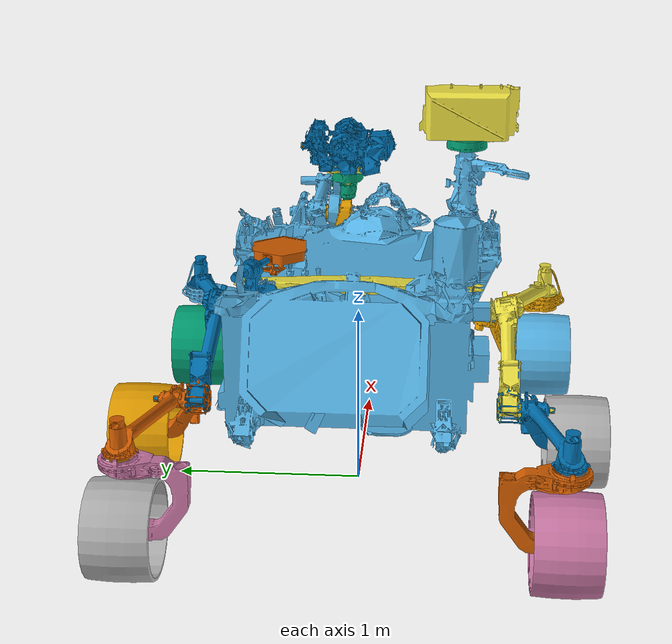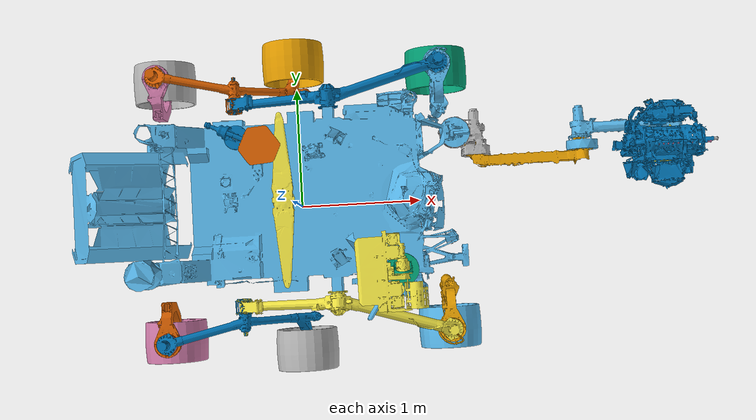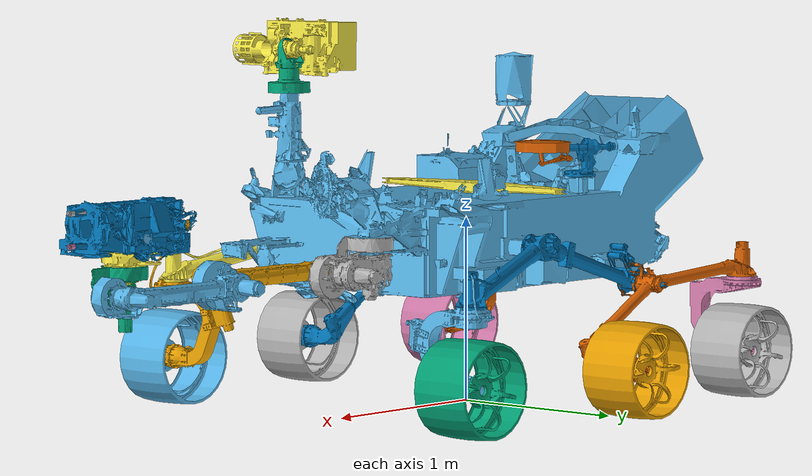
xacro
<?xml version="1.0" ?>

<robot name="perseverance" xmlns:xacro="http://www.ros.org/wiki/xacro">

  <xacro:property name="robot_name" value="perseverance" />
  <xacro:property name="mu1" value="100"/>
  <xacro:property name="mu2" value="100"/>

  <xacro:include filename="$(find m2020_urdf_models)/urdf/m2020.traclabs.urdf.xacro" />
  <xacro:include filename="$(find m2020_urdf_models)/urdf/gazebo/m2020.gazebo.components.xacro" />
  <xacro:include filename="$(find m2020_urdf_models)/urdf/gazebo/m2020.gazebo.controllers.xacro" />

  <!-- Parameters wheels -->
  <gazebo reference="LF_DRIVE">
    <implicitSpringDamper>1</implicitSpringDamper>
  </gazebo>
  <gazebo reference="LM_DRIVE">
    <implicitSpringDamper>1</implicitSpringDamper>
  </gazebo>
  <gazebo reference="LR_DRIVE">
    <implicitSpringDamper>1</implicitSpringDamper>
  </gazebo>
  <gazebo reference="RF_DRIVE">
    <implicitSpringDamper>1</implicitSpringDamper>
  </gazebo>
  <gazebo reference="RM_DRIVE">
    <implicitSpringDamper>1</implicitSpringDamper>
  </gazebo>
  <gazebo reference="RR_DRIVE">
    <implicitSpringDamper>1</implicitSpringDamper>
  </gazebo>

  <gazebo reference="Body_WheelLeftFront">
    <kp>1000000.0</kp>
    <kd>100.0</kd>
    <mu1>${mu1}</mu1>
    <mu2>${mu2}</mu2>
    <fdir1>1 0 0</fdir1>
    <maxVel>1.0</maxVel>
    <minDepth>0.01</minDepth>
  </gazebo>

  <gazebo reference="Body_WheelLeftRear">
    <kp>1000000.0</kp>
    <kd>100.0</kd>
    <mu1>${mu1}</mu1>
    <mu2>${mu2}</mu2>
    <fdir1>1 0 0</fdir1>
    <maxVel>1.0</maxVel>
    <minDepth>0.01</minDepth>
  </gazebo>

  <gazebo reference="Body_WheelLeftMiddle">
    <kp>1000000.0</kp>
    <kd>100.0</kd>
    <mu1>${mu1}</mu1>
    <mu2>${mu2}</mu2>
    <maxVel>1.0</maxVel>
    <minDepth>0.01</minDepth>
  </gazebo>

  <gazebo reference="Body_WheelRightFront">
    <kp>1000000.0</kp>
    <kd>100.0</kd>
    <mu1>${mu1}</mu1>
    <mu2>${mu2}</mu2>
    <maxVel>1.0</maxVel>
    <minDepth>0.01</minDepth>
  </gazebo>

  <gazebo reference="Body_WheelRightRear">
    <kp>1000000.0</kp>
    <kd>100.0</kd>
    <mu1>${mu1}</mu1>
    <mu2>${mu2}</mu2>
    <maxVel>1.0</maxVel>
    <minDepth>0.01</minDepth>
  </gazebo>

  <gazebo reference="Body_WheelRightMiddle">
    <kp>1000000.0</kp>
    <kd>100.0</kd>
    <mu1>${mu1}</mu1>
    <mu2>${mu2}</mu2>
    <maxVel>1.0</maxVel>
    <minDepth>0.01</minDepth>
  </gazebo>

</robot>

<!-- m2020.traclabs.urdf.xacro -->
<!-- m2020.urdf.xacro : File that was mostly copied similar to the original, with small fixes such as changing .gtlif to .dae -->
<!-- m2020.gazebo.urdf.xacro: File that was vastly modified by TRACLabs to work with Gazebo -->
<robot name="perseverance" xmlns:xacro="http://www.ros.org/wiki/xacro">

  <!-- Set wheel MIDDLE links to be smaller, so they don't touch the floor (so we only use the front and back for diff driving)-->

  <xacro:include filename="$(find m2020_urdf_models)/urdf/gazebo/m2020.gazebo.component_macros.xacro"/>

  <xacro:property name="M_PI" value="3.14159"/>

  <xacro:property name="arm_joint_vel" value="0.6" /> <!-- original value: 1.79769e+308 -->
  <xacro:property name="head_joint_vel" value="1.0" /> <!-- original value: 1.79769e+308 -->
  <xacro:property name="arm_default_effort" value="100.0" /> <!-- original value: 1.79769e+308 -->
  <xacro:property name="stabilizer_default_vel" value="0.5"/> <!-- original value: 1.79769e+308 -->
  <xacro:property name="stabilizer_default_effort" value="50"/> <!-- original value: 1.79769e+308 -->

  <xacro:property name="arm_default_damping" value="250.0"/>
  <xacro:property name="arm_default_friction" value="10.0"/>
  <xacro:property name="default_mass" value="3.0" />
  <xacro:property name="default_ixx" value="0.2" />
  <xacro:property name="default_iyy" value="0.2" />
  <xacro:property name="default_izz" value="0.2" />

  <xacro:property name="link4_ixx" value="0.05" />
  <xacro:property name="link4_iyy" value="0.05" />
  <xacro:property name="link4_izz" value="0.05" />

  <xacro:property name="link5_ixx" value="0.05" />
  <xacro:property name="link5_iyy" value="0.05" />
  <xacro:property name="link5_izz" value="0.05" />

  <xacro:property name="stabilizer_mass" value="0.5"/>
  <xacro:property name="stabilizer_ixx" value="0.01" />
  <xacro:property name="stabilizer_iyy" value="0.01" />
  <xacro:property name="stabilizer_izz" value="0.01" />

  <xacro:property name="cap_mass" value="0.1"/>
  <xacro:property name="cap_ixx" value="0.005" />
  <xacro:property name="cap_iyy" value="0.005" />
  <xacro:property name="cap_izz" value="0.005" />

  <xacro:property name="turret_mass" value="1.0"/>
  <xacro:property name="turret_ixx" value="0.1" />
  <xacro:property name="turret_iyy" value="0.1" />
  <xacro:property name="turret_izz" value="0.1" />

  <!-- For link with no visual, no collision, just a frame -->
  <xacro:property name="tiny_mass" value="0.001"/>
  <xacro:property name="tiny_ixx" value="0.00001" />
  <xacro:property name="tiny_iyy" value="0.00001" />
  <xacro:property name="tiny_izz" value="0.00001" />

  <xacro:property name="head_damping" value="1.0"/>
  <xacro:property name="head_friction" value="10.0"/>
  <xacro:property name="head_effort" value="100.0" />

  <xacro:property name="wheel_mass" value="10.0" />
  <xacro:property name="wheel_ixx" value="${0.0254*wheel_mass}" />
  <xacro:property name="wheel_iyy" value="${0.0325*wheel_mass}" />
  <xacro:property name="wheel_izz" value="${0.0254*wheel_mass}" />

  <xacro:property name="wheel_effort" value="1000.0" />
  <xacro:property name="wheel_velocity" value="20.0" />

  <xacro:property name="wheel_radius" value="0.255" />
  <xacro:property name="wheel_width" value="0.331" />

	<link name="base_footprint"/>

	<link name="Body_Chassis">
		<inertial>
			<origin xyz="0.09002 0 -1.13338" rpy="0 -0 0"/>
			<mass value="100"/>
			<inertia ixx="0.714" ixy="0" ixz="0" iyy="2.348" iyz="0" izz="2.723"/>
		</inertial>
		<visual name="VisGeom_CHASSIS">
			<origin xyz="0.09002 0 -1.13338" rpy="0 -0 0"/>
			<geometry>
				<mesh filename="package://m2020_urdf_models/rover/meshes/CHASSIS.dae" scale="1 1 1"/>
			</geometry>
		</visual>
		<collision name="CollGeom_CHASSIS">
			<origin xyz="0.09002 0 -1.13338" rpy="0 -0 0"/>
			<geometry>
				<mesh filename="package://m2020_urdf_models/rover/meshes/low_res/CHASSIS_low_res.stl" scale="1 1 1"/>
			</geometry>
		</collision>
	</link>

	<link name="Body_MHS_DebrisShield">
	</link>
	<link name="Body_Differential">
		<inertial>
			<origin xyz="0 0 0" rpy="0 -0 0"/>
			<mass value="${default_mass}"/>
			<inertia ixx="${default_ixx}" ixy="0" ixz="0" iyy="${default_iyy}" iyz="0" izz="${default_izz}"/>
		</inertial>
		<visual name="VisGeom_CenterDifferential">
			<origin xyz="0.142 0 0" rpy="0 -0 0"/>
			<geometry>
				<mesh filename="package://m2020_urdf_models/rover/meshes/CenterDifferential.dae" scale="1 1 1"/>
			</geometry>
		</visual>
		<collision name="CollGeom_CenterDifferential">
			<origin xyz="0.142 0 0" rpy="0 -0 0"/>
			<geometry>
				<mesh filename="package://m2020_urdf_models/rover/meshes/low_res/CenterDifferential_low_res.stl" scale="1 1 1"/>
			</geometry>
		</collision>
	</link>
	<link name="Body_RockerLeft">
		<inertial>
			<origin xyz="0 0 0" rpy="0 -0 0"/>
			<mass value="${default_mass}"/>
			<inertia ixx="${default_ixx}" ixy="0" ixz="0" iyy="${default_iyy}" iyz="0" izz="${default_izz}"/>
		</inertial>
		<visual name="VisGeom_Left_Rocker">
			<origin xyz="-0.214 0.79959 -0.2405" rpy="0 -0 0"/>
			<geometry>
				<mesh filename="package://m2020_urdf_models/rover/meshes/Left_Rocker.dae" scale="1 1 1"/>
			</geometry>
		</visual>
		<collision name="CollGeom_Left_Rocker">
			<origin xyz="-0.214 0.79959 -0.2405" rpy="0 -0 0"/>
			<geometry>
				<mesh filename="package://m2020_urdf_models/rover/meshes/low_res/Left_Rocker_low_res.stl" scale="1 1 1"/>
			</geometry>
		</collision>
	</link>
	<link name="Body_BogieLeft">
		<inertial>
			<origin xyz="0.0 0 0" rpy="0 -0 0"/>
			<mass value="${default_mass}"/>
			<inertia ixx="${default_ixx}" ixy="0" ixz="0" iyy="${default_iyy}" iyz="0" izz="${default_izz}"/>
		</inertial>
		<visual name="VisGeom_Left_Bogie">
			<origin xyz="0.54 0.91959 -0.4705" rpy="0 -0 0"/>
			<geometry>
				<mesh filename="package://m2020_urdf_models/rover/meshes/Left_Bogie.dae" scale="1 1 1"/>
			</geometry>
		</visual>
		<collision name="CollGeom_Left_Bogie">
			<origin xyz="0.54 0.91959 -0.4705" rpy="0 -0 0"/>
			<geometry>
				<mesh filename="package://m2020_urdf_models/rover/meshes/low_res/Left_Bogie_low_res.stl" scale="1 1 1"/>
			</geometry>
		</collision>
	</link>
	<link name="Body_SteerLeftRear">
		<inertial>
			<origin xyz="0 0 0" rpy="0 -0 0"/>
			<mass value="${default_mass}"/>
			<inertia ixx="${default_ixx}" ixy="0" ixz="0" iyy="${default_iyy}" iyz="0" izz="${default_izz}"/>
		</inertial>
		<visual name="VisGeom_Steer_LeftRear">
			<origin xyz="1.165 1.0625 -0.8705" rpy="0 -0 0"/>
			<geometry>
				<mesh filename="package://m2020_urdf_models/rover/meshes/Steer_LeftRear.dae" scale="1 1 1"/>
			</geometry>
		</visual>
		<collision name="CollGeom_Steer_LeftRear">
			<origin xyz="1.165 1.0625 -0.8705" rpy="0 -0 0"/>
			<geometry>
				<mesh filename="package://m2020_urdf_models/rover/meshes/low_res/Steer_LeftRear_low_res.stl" scale="1 1 1"/>
			</geometry>
		</collision>
	</link>
	<link name="Body_WheelLeftRear">
		<inertial>
			<origin xyz="0 0 0" rpy="0 0 0"/>
			<mass value="${wheel_mass}"/>
			<inertia ixx="${wheel_ixx}" ixy="0" ixz="0" iyy="${wheel_iyy}" iyz="0" izz="${wheel_izz}"/>
		</inertial>
		<visual name="VisGeom_Wheel_LeftRear">
			<origin xyz="1.165 1.0625 -0.8705" rpy="0 -0 0"/>
			<geometry>
				<mesh filename="package://m2020_urdf_models/rover/meshes/Wheel_LeftRear.dae" scale="1 1 1"/>
			</geometry>
		</visual>
		<collision name="ColGeom_Wheel_LeftRear">
          <origin xyz="0 0 0" rpy="${M_PI/2} 0 0" />
          <geometry>
            <cylinder radius="${wheel_radius-0.0001}" length="${wheel_width}"/>
          </geometry>
		</collision>
	</link>
	<link name="Body_WheelLeftMiddle">
		<inertial>
			<origin xyz="0 0 0" rpy="0 -0 0"/>
			<mass value="${wheel_mass}"/>
			<inertia ixx="${wheel_ixx}" ixy="0" ixz="0" iyy="${wheel_iyy}" iyz="0" izz="${wheel_izz}"/>
		</inertial>
		<visual name="VisGeom_Wheel_LeftMiddle">
			<origin xyz="0.09002 1.1845 -0.8705" rpy="0 -0 0"/>
			<geometry>
				<mesh filename="package://m2020_urdf_models/rover/meshes/Wheel_LeftMiddle.dae" scale="1 1 1"/>
			</geometry>
		</visual>
		<collision name="ColGeom_Wheel_LeftMiddle">
          <origin xyz="0 0 0" rpy="${M_PI/2} 0 0" />
          <geometry>
            <cylinder radius="${wheel_radius-0.0001}" length="${wheel_width}"/>
          </geometry>
		</collision>
	</link>
	<link name="Body_SteerLeftFront">
		<inertial>
			<origin xyz="-1.095 1.0625 -0.8705" rpy="0 -0 0"/>
			<mass value="${default_mass}"/>
			<inertia ixx="${default_ixx}" ixy="0" ixz="0" iyy="${default_iyy}" iyz="0" izz="${default_izz}"/>
		</inertial>
		<visual name="VisGeom_Steer_LeftFront">
			<origin xyz="-1.095 1.0625 -0.8705" rpy="0 -0 0"/>
			<geometry>
				<mesh filename="package://m2020_urdf_models/rover/meshes/Steer_LeftFront.dae" scale="1 1 1"/>
			</geometry>
		</visual>
		<collision name="CollGeom_Steer_LeftFront">
			<origin xyz="-1.095 1.0625 -0.8705" rpy="0 -0 0"/>
			<geometry>
				<mesh filename="package://m2020_urdf_models/rover/meshes/low_res/Steer_LeftFront_low_res.stl" scale="1 1 1"/>
			</geometry>
		</collision>
	</link>
	<link name="Body_WheelLeftFront">
		<inertial>
			<origin xyz="0 0 0" rpy="0 -0 0"/>
			<mass value="${wheel_mass}"/>
			<inertia ixx="${wheel_ixx}" ixy="0" ixz="0" iyy="${wheel_iyy}" iyz="0" izz="${wheel_izz}"/>
		</inertial>
		<visual name="VisGeom_Wheel_LeftFront">
			<origin xyz="-1.095 1.0625 -0.8705" rpy="0 -0 0"/>
			<geometry>
				<mesh filename="package://m2020_urdf_models/rover/meshes/Wheel_LeftFront.dae" scale="1 1 1"/>
			</geometry>
		</visual>
		<collision name="ColGeom_Wheel_LeftFront">
          <origin xyz="0 0 0" rpy="${M_PI/2} 0 0" />
          <geometry>
            <cylinder radius="${wheel_radius-0.0001}" length="${wheel_width}"/>
          </geometry>
		</collision>
	</link>
	<link name="Body_RockerRight">
		<inertial>
			<origin xyz="0 0 0" rpy="0 0 0"/>
			<mass value="${default_mass}"/>
			<inertia ixx="${default_ixx}" ixy="0" ixz="0" iyy="${default_iyy}" iyz="0" izz="${default_izz}"/>
		</inertial>
		<visual name="VisGeom_Right_Rocker">
			<origin xyz="-0.214 -0.79959 -0.2405" rpy="0 -0 0"/>
			<geometry>
				<mesh filename="package://m2020_urdf_models/rover/meshes/Right_Rocker.dae" scale="1 1 1"/>
			</geometry>
		</visual>
		<collision name="ColGeom_Right_Rocker">
			<origin xyz="-0.214 -0.79959 -0.2405" rpy="0 -0 0"/>
			<geometry>
				<mesh filename="package://m2020_urdf_models/rover/meshes/low_res/Right_Rocker_low_res.stl" scale="1 1 1"/>
			</geometry>
		</collision>

	</link>
	<link name="Body_BogieRight">
		<inertial>
			<origin xyz="0 0 0" rpy="0 0 0"/>
			<mass value="${default_mass}"/>
			<inertia ixx="${default_ixx}" ixy="0" ixz="0" iyy="${default_iyy}" iyz="0" izz="${default_izz}"/>
		</inertial>
		<visual name="VisGeom_Right_Bogie">
			<origin xyz="0.54 -0.91959 -0.4705" rpy="0 -0 0"/>
			<geometry>
				<mesh filename="package://m2020_urdf_models/rover/meshes/Right_Bogie.dae" scale="1 1 1"/>
			</geometry>
		</visual>
		<collision name="ColGeom_Right_Bogie">
			<origin xyz="0.54 -0.91959 -0.4705" rpy="0 -0 0"/>
			<geometry>
				<mesh filename="package://m2020_urdf_models/rover/meshes/low_res/Right_Bogie_low_res.stl" scale="1 1 1"/>
			</geometry>
		</collision>
	</link>
	<link name="Body_SteerRightRear">
		<inertial>
			<origin xyz="0 0 0" rpy="0 0 0"/>
			<mass value="${default_mass}"/>
			<inertia ixx="${default_ixx}" ixy="0" ixz="0" iyy="${default_iyy}" iyz="0" izz="${default_izz}"/>
		</inertial>
		<visual name="VisGeom_Steer_RightRear">
			<origin xyz="1.165 -1.0625 -0.8705" rpy="0 -0 0"/>
			<geometry>
				<mesh filename="package://m2020_urdf_models/rover/meshes/Steer_RightRear.dae" scale="1 1 1"/>
			</geometry>
		</visual>
		<collision name="CollGeom_Steer_RightRear">
			<origin xyz="1.165 -1.0625 -0.8705" rpy="0 -0 0"/>
			<geometry>
				<mesh filename="package://m2020_urdf_models/rover/meshes/low_res/Steer_RightRear_low_res.stl" scale="1 1 1"/>
			</geometry>
		</collision>
	</link>
	<link name="Body_WheelRightRear">
		<inertial>
			<origin xyz="0 0 0" rpy="0 -0 0"/>
			<mass value="${wheel_mass}"/>
			<inertia ixx="${wheel_ixx}" ixy="0" ixz="0" iyy="${wheel_iyy}" iyz="0" izz="${wheel_izz}"/>
		</inertial>
		<visual name="VisGeom_Wheel_RightRear">
			<origin xyz="1.165 -1.0625 -0.8705" rpy="0 -0 0"/>
			<geometry>
				<mesh filename="package://m2020_urdf_models/rover/meshes/Wheel_RightRear.dae" scale="1 1 1"/>
			</geometry>
		</visual>
		<collision name="ColGeom_Wheel_RightRear">
          <origin xyz="0 0 0" rpy="${M_PI/2} 0 0" />
          <geometry>
            <cylinder radius="${wheel_radius-0.0001}" length="${wheel_width}"/>
          </geometry>
		</collision>
	</link>
	<link name="Body_WheelRightMiddle">
		<inertial>
			<origin xyz="0 0 0" rpy="0 -0 0"/>
			<mass value="${wheel_mass}"/>
			<inertia ixx="${wheel_ixx}" ixy="0" ixz="0" iyy="${wheel_iyy}" iyz="0" izz="${wheel_izz}"/>
		</inertial>
		<visual name="VisGeom_Wheel_RightMiddle">
			<origin xyz="0.09002 -1.1845 -0.8705" rpy="0 -0 0"/>
			<geometry>
				<mesh filename="package://m2020_urdf_models/rover/meshes/Wheel_RightMiddle.dae" scale="1 1 1"/>
			</geometry>
		</visual>
		<collision name="ColGeom_Wheel_RightMiddle">
          <origin xyz="0 0 0" rpy="${M_PI/2} 0 0" />
          <geometry>
            <cylinder radius="${wheel_radius-0.0001}" length="${wheel_width}"/>
          </geometry>
		</collision>
	</link>
	<link name="Body_SteerRightFront">
		<inertial>
			<origin xyz="0 0 0" rpy="0 -0 0"/>
			<mass value="${default_mass}"/>
			<inertia ixx="${default_ixx}" ixy="0" ixz="0" iyy="${default_iyy}" iyz="0" izz="${default_izz}"/>
		</inertial>
		<visual name="VisGeom_Steer_RightFront">
			<origin xyz="-1.095 -1.0625 -0.8705" rpy="0 -0 0"/>
			<geometry>
				<mesh filename="package://m2020_urdf_models/rover/meshes/Steer_RightFront.dae" scale="1 1 1"/>
			</geometry>
		</visual>
		<collision name="CollGeom_Steer_RightFront">
			<origin xyz="-1.095 -1.0625 -0.8705" rpy="0 -0 0"/>
			<geometry>
				<mesh filename="package://m2020_urdf_models/rover/meshes/low_res/Steer_RightFront_low_res.stl" scale="1 1 1"/>
			</geometry>
		</collision>
	</link>
	<link name="Body_WheelRightFront">
		<inertial>
			<origin xyz="0 0 0" rpy="0 -0 0"/>
			<mass value="${wheel_mass}"/>
			<inertia ixx="${wheel_ixx}" ixy="0" ixz="0" iyy="${wheel_iyy}" iyz="0" izz="${wheel_izz}"/>
		</inertial>
		<visual name="VisGeom_Wheel_RightFront">
			<origin xyz="-1.095 -1.0625 -0.8705" rpy="0 -0 0"/>
			<geometry>
				<mesh filename="package://m2020_urdf_models/rover/meshes/Wheel_RightFront.dae" scale="1 1 1"/>
			</geometry>
		</visual>
		<collision name="ColGeom_Wheel_RightFront">
          <origin xyz="0 0 0" rpy="${M_PI/2} 0 0" />
          <geometry>
            <cylinder radius="${wheel_radius-0.0001}" length="${wheel_width}"/>
          </geometry>
		</collision>
	</link>
	<link name="Body_RSM_AZ">
		<inertial>
			<origin xyz="0 0 0" rpy="0 -0 0"/>
			<mass value="${default_mass}"/>
			<inertia ixx="${default_ixx}" ixy="0" ixz="0" iyy="${default_iyy}" iyz="0" izz="${default_izz}"/>
		</inertial>
		<visual name="VisGeom_RSM">
			<origin xyz="-0.714017 -0.559028 0.78589" rpy="0 -0 0"/>
			<geometry>
				<mesh filename="package://m2020_urdf_models/rover/meshes/RSM.dae" scale="1 1 1"/>
			</geometry>
		</visual>
		<collision name="CollGeom_RSM">
			<origin xyz="-0.714017 -0.559028 0.78589" rpy="0 -0 0"/>
			<geometry>
				<mesh filename="package://m2020_urdf_models/rover/meshes/low_res/RSM_low_res.stl" scale="1 1 1"/>
			</geometry>
		</collision>
	</link>
	<link name="Body_RSM_EL">
		<inertial>
			<origin xyz="0 0 0" rpy="0 -0 0"/>
			<mass value="${default_mass}"/>
			<inertia ixx="${default_ixx}" ixy="0" ixz="0" iyy="${default_iyy}" iyz="0" izz="${default_izz}"/>
		</inertial>
		<visual name="VisGeom_RSM_HEAD">
			<origin xyz="-0.714017 -0.559028 0.78589" rpy="0 -0 0"/>
			<geometry>
				<mesh filename="package://m2020_urdf_models/rover/meshes/RSM_Head.dae" scale="1 1 1"/>
			</geometry>
		</visual>
		<collision name="CollGeom_RSM_HEAD">
			<origin xyz="-0.714017 -0.559028 0.78589" rpy="0 -0 0"/>
			<geometry>
				<mesh filename="package://m2020_urdf_models/rover/meshes/low_res/RSM_Head_low_res.stl" scale="1 1 1"/>
			</geometry>
		</collision>
	</link>
	<link name="Body_HGA_AZ">
		<inertial>
			<origin xyz="0 0 0" rpy="0 0 0"/>
			<mass value="${default_mass}"/>
			<inertia ixx="${default_ixx}" ixy="0" ixz="0" iyy="${default_iyy}" iyz="0" izz="${default_izz}"/>
		</inertial>
		<visual name="VisGeom_HGA_AZ">
			<origin xyz="0.46 0.475 -0.0005" rpy="0 -0 0"/>
			<geometry>
				<mesh filename="package://m2020_urdf_models/rover/meshes/HGA_AZ.dae" scale="1 1 1"/>
			</geometry>
		</visual>
		<collision name="CollGeom_HGA_AZ">
			<origin xyz="0.46 0.475 -0.0005" rpy="0 -0 0"/>
			<geometry>
				<mesh filename="package://m2020_urdf_models/rover/meshes/low_res/HGA_AZ_low_res.stl" scale="1 1 1"/>
			</geometry>
		</collision>
	</link>
	<link name="Body_HGA_EL">
		<inertial>
			<origin xyz="0 0 0" rpy="0 0 0"/>
			<mass value="${default_mass}"/>
			<inertia ixx="${default_ixx}" ixy="0" ixz="0" iyy="${default_iyy}" iyz="0" izz="${default_izz}"/>
		</inertial>
		<visual name="VisGeom_HGA_EL">
			<origin xyz="0.46 0.475 0.2475" rpy="0 -0 0"/>
			<geometry>
				<mesh filename="package://m2020_urdf_models/rover/meshes/HGA_EL.dae" scale="1 1 1"/>
			</geometry>
		</visual>
		<collision name="CollGeom_HGA_EL">
			<origin xyz="0.46 0.475 0.2475" rpy="0 -0 0"/>
			<geometry>
				<mesh filename="package://m2020_urdf_models/rover/meshes/low_res/HGA_EL_low_res.stl" scale="1 1 1"/>
			</geometry>
		</collision>
	</link>
	<link name="Body_RA_Base">
		<inertial>
			<origin xyz="0 0 0" rpy="0 0 0"/>
			<mass value="${tiny_mass}"/>
			<inertia ixx="${tiny_ixx}" ixy="0" ixz="0" iyy="${tiny_iyy}" iyz="0" izz="${tiny_izz}"/>
		</inertial>
	</link>
	<link name="Body_RA_Link1">
		<inertial>
			<origin xyz="0 0 0" rpy="0 0 0"/>
			<mass value="${default_mass}"/>
			<inertia ixx="${default_ixx}" ixy="0" ixz="0" iyy="${default_iyy}" iyz="0" izz="${default_izz}"/>
		</inertial>
		<visual name="VisGeom_Arm_LINK_1">
			<origin xyz="-1.1756 0.4515 -0.3116" rpy="0 -0 0"/>
			<geometry>
				<mesh filename="package://m2020_urdf_models/rover/meshes/Arm_LINK_1.dae" scale="1 1 1"/>
			</geometry>
		</visual>
		<collision name="ColGeom_Arm_LINK_1">
			<origin xyz="-1.1756 0.4515 -0.3116" rpy="0 -0 0"/>
			<geometry>
				<mesh filename="package://m2020_urdf_models/rover/meshes/low_res/Arm_LINK_1_low_res.stl" scale="1 1 1"/>
			</geometry>
		</collision>
	</link>
	<link name="Body_RA_Link2">
		<inertial>
			<origin xyz="0 0 0" rpy="0 -0 0"/>
			<mass value="${default_mass}"/>
			<inertia ixx="${default_ixx}" ixy="0" ixz="0" iyy="${default_iyy}" iyz="0" izz="${default_izz}"/>
		</inertial>
		<visual name="VisGeom_Arm_LINK_2">
			<origin xyz="-1.3416 0.4515 -0.3116" rpy="0 -0 0"/>
			<geometry>
				<mesh filename="package://m2020_urdf_models/rover/meshes/Arm_LINK_2.dae" scale="1 1 1"/>
			</geometry>
		</visual>
		<collision name="ColGeom_Arm_LINK_2">
			<origin xyz="-1.3416 0.4515 -0.3116" rpy="0 -0 0"/>
			<geometry>
				<mesh filename="package://m2020_urdf_models/rover/meshes/low_res/Arm_LINK_2_low_res.stl" scale="1 1 1"/>
			</geometry>
		</collision>
	</link>
	<link name="Body_RA_Link3">
		<inertial>
			<origin xyz="0 0 0" rpy="0 0 0"/>
			<mass value="${default_mass}"/>
			<inertia ixx="0.1" ixy="0" ixz="0" iyy="0.1" iyz="0" izz="0.1"/>
		</inertial>
		<visual name="VisGeom_Arm_LINK_3">
			<origin xyz="-2.161 0.4515 -0.3116" rpy="0 -0 0"/>
			<geometry>
				<mesh filename="package://m2020_urdf_models/rover/meshes/Arm_LINK_3.dae" scale="1 1 1"/>
			</geometry>
		</visual>
		<collision name="ColGeom_Arm_LINK_3">
			<origin xyz="-2.161 0.4515 -0.3116" rpy="0 -0 0"/>
			<geometry>
				<mesh filename="package://m2020_urdf_models/rover/meshes/low_res/Arm_LINK_3_low_res.stl" scale="1 1 1"/>
			</geometry>
		</collision>
	</link>
	<link name="Body_RA_Link4">
		<inertial>
			<origin xyz="0 0 0" rpy="0 0 0"/>
			<mass value="${default_mass}"/>
			<inertia ixx="${link4_ixx}" ixy="0" ixz="0" iyy="${link4_iyy}" iyz="0" izz="${link4_izz}"/>
		</inertial>
		<visual name="VisGeom_Arm_LINK_4">
			<origin xyz="-2.9143 0.4515 -0.3116" rpy="0 -0 0"/>
			<geometry>
				<mesh filename="package://m2020_urdf_models/rover/meshes/Arm_LINK_4.dae" scale="1 1 1"/>
			</geometry>
		</visual>
		<collision name="ColGeom_Arm_LINK_4">
			<origin xyz="-2.9143 0.4515 -0.3116" rpy="0 -0 0"/>
			<geometry>
				<mesh filename="package://m2020_urdf_models/rover/meshes/low_res/Arm_LINK_4_low_res.stl" scale="1 1 1"/>
			</geometry>
		</collision>
	</link>
	<link name="Body_RA_Link5">
	    <inertial>
			<origin xyz="0 0 0" rpy="0 0 0"/>
			<mass value="${default_mass}"/>
			<inertia ixx="${link5_ixx}" ixy="0" ixz="0" iyy="${link5_iyy}" iyz="0" izz="${link5_izz}"/>
		</inertial>
		<visual name="VisGeom_Arm_LINK_5">
			<origin xyz="-2.7386 0.2724 -0.3116" rpy="0 -0 0"/>
			<geometry>
				<mesh filename="package://m2020_urdf_models/rover/meshes/Arm_LINK_5.dae" scale="1 1 1"/>
			</geometry>
		</visual>
		<collision name="CollGeom_Arm_LINK_5">
			<origin xyz="-2.7386 0.2724 -0.3116" rpy="0 -0 0"/>
			<geometry>
				<mesh filename="package://m2020_urdf_models/rover/meshes/low_res/Arm_LINK_5_low_res.stl" scale="1 1 1"/>
			</geometry>
		</collision>
	</link>
	<link name="Body_Turret">
		<inertial>
			<origin xyz="0 0 0" rpy="0 0 0"/>
			<mass value="${turret_mass}"/>
			<inertia ixx="${turret_ixx}" ixy="0" ixz="0" iyy="${turret_iyy}" iyz="0" izz="${turret_izz}"/>
		</inertial>
		<visual name="VisGeom_Turret">
			<origin xyz="0 0 0" rpy="0 -0 0"/>
			<geometry>
				<mesh filename="package://m2020_urdf_models/rover/meshes/Turret.dae" scale="1 1 1"/>
			</geometry>
		</visual>
		<collision name="ColGeom_Turret">
			<origin xyz="0 0 0" rpy="0 -0 0"/>
			<geometry>
				<mesh filename="package://m2020_urdf_models/rover/meshes/low_res/Turret_low_res.stl" scale="1 1 1"/>
			</geometry>
		</collision>
	</link>
	<link name="Body_CorerFeed">
		<!-- Commented out TRACLabs -->
		<!-- Commented out TRACLabs -->
	</link>
	<link name="Body_StabilizerFar">
		<inertial>
			<origin xyz="0 0 0" rpy="0 0 0"/>
			<mass value="${stabilizer_mass}"/>
			<inertia ixx="${stabilizer_ixx}" ixy="0" ixz="0" iyy="${stabilizer_iyy}" iyz="0" izz="${stabilizer_izz}"/>
		</inertial>
		<visual name="VisGeom_StabilizerFar">
			<origin xyz="0.208499 -5.1e-05 -3.438e-05" rpy="0 -0 0"/>
			<geometry>
				<mesh filename="package://m2020_urdf_models/rover/meshes/StabilizerFarInTurret.dae" scale="1 1 1"/>
			</geometry>
		</visual>
		<collision name="CollGeom_StabilizerFar">
			<origin xyz="0.208499 -5.1e-05 -3.438e-05" rpy="0 -0 0"/>
			<geometry>
				<mesh filename="package://m2020_urdf_models/rover/meshes/low_res/StabilizerFarInTurret_low_res.stl" scale="1 1 1"/>
			</geometry>
		</collision>
	</link>
	<link name="Body_StabilizerNear">
		<inertial>
			<origin xyz="0 0 0" rpy="0 -0 0"/>
			<mass value="${stabilizer_mass}"/>
			<inertia ixx="${stabilizer_ixx}" ixy="0" ixz="0" iyy="${stabilizer_iyy}" iyz="0" izz="${stabilizer_izz}"/>
		</inertial>
		<visual name="VisGeom_StabilizerNear">
			<origin xyz="0.208499 -5.1e-05 -3.438e-05" rpy="0 -0 0"/>
			<geometry>
				<mesh filename="package://m2020_urdf_models/rover/meshes/StabilizerNearInTurret.dae" scale="1 1 1"/>
			</geometry>
		</visual>
		<collision name="CollGeom_StabilizerNear">
			<origin xyz="0.208499 -5.1e-05 -3.438e-05" rpy="0 -0 0"/>
			<geometry>
				<mesh filename="package://m2020_urdf_models/rover/meshes/low_res/StabilizerNearInTurret_low_res.stl" scale="1 1 1"/>
			</geometry>
		</collision>
	</link>
	<link name="Body_WATSON_Cap">
		<inertial>
			<origin xyz="0 0 0" rpy="0 0 0"/>
			<mass value="${cap_mass}"/>
			<inertia ixx="${cap_ixx}" ixy="0" ixz="0" iyy="${cap_iyy}" iyz="0" izz="${cap_izz}"/>
		</inertial>
		<visual name="VisGeom_WATSON_Cap">
			<origin xyz="-2.6025 0.581204 0.0309103" rpy="0 -0 0"/>
			<geometry>
				<mesh filename="package://m2020_urdf_models/rover/meshes/WATSON_Camera_Cap.dae" scale="1 1 1"/>
			</geometry>
		</visual>
		<collision name="CollGeom_WATSON_Cap">
			<origin xyz="-2.6025 0.581204 0.0309103" rpy="0 -0 0"/>
			<geometry>
				<mesh filename="package://m2020_urdf_models/rover/meshes/low_res/WATSON_Camera_Cap_low_res.stl" scale="1 1 1"/>
			</geometry>
		</collision>
	</link>
	<link name="Body_SHERLOC_Cap">
		<inertial>
			<origin xyz="0 0 0" rpy="0 0 0"/>
			<mass value="${cap_mass}"/>
			<inertia ixx="${cap_ixx}" ixy="0" ixz="0" iyy="${cap_iyy}" iyz="0" izz="${cap_izz}"/>
		</inertial>
		<visual name="VisGeom_SHERLOC_Cap">
			<origin xyz="-2.86084 0.58439 -0.0124626" rpy="0 -0 0"/>
			<geometry>
				<mesh filename="package://m2020_urdf_models/rover/meshes/ContextImager_Cap.dae" scale="1 1 1"/>
			</geometry>
		</visual>
		<collision name="CollGeom_SHERLOC_Cap">
			<origin xyz="-2.86084 0.58439 -0.0124626" rpy="0 -0 0"/>
			<geometry>
				<mesh filename="package://m2020_urdf_models/rover/meshes/low_res/ContextImager_Cap_low_res.stl" scale="1 1 1"/>
			</geometry>
		</collision>
	</link>
	<link name="Frame_RNAV"/>
	<link name="Frame_RMECH"/>
	<link name="Frame_FHCB"/>
	<link name="Frame_FHC1"/>
	<link name="Frame_FHC2"/>
	<link name="Frame_FHC3"/>
	<link name="Frame_FHC4"/>
	<link name="Frame_FHC1_FOV"/>
	<link name="Frame_FHC2_FOV"/>
	<link name="Frame_FHC3_FOV"/>
	<link name="Frame_FHC4_FOV"/>
	<link name="Frame_RHC1"/>
	<link name="Frame_RHC2"/>
	<link name="Frame_RHC1_FOV"/>
	<link name="Frame_RHC2_FOV"/>
	<link name="Frame_ATS1"/>
	<link name="Frame_ATS2"/>
	<link name="Frame_ATS3"/>
	<link name="Frame_ATS4"/>
	<link name="Frame_ATS5"/>
	<link name="Frame_HS"/>
	<link name="Frame_ICU"/>
	<link name="Frame_RDS"/>
	<link name="Frame_TIRS"/>
	<link name="Frame_WS1"/>
	<link name="Frame_WS2"/>
	<link name="Frame_MOXIE"/>
	<link name="Frame_MI"/>
	<link name="Frame_MAZ"/>
	<link name="Frame_MEL"/>
	<link name="Frame_SCI"/>
	<link name="Frame_SCRMI"/>
	<link name="Frame_SCLIBS"/>
	<link name="Frame_SCIR"/>
	<link name="Frame_MCL"/>
	<link name="Frame_MCR"/>
	<link name="Frame_NCL"/>
	<link name="Frame_NCR"/>
	<link name="Frame_NCL_FOV"/>
	<link name="Frame_NCR_FOV"/>
	<link name="Frame_ROCKER_L"/>
	<link name="Frame_ROCKER_R"/>
	<link name="Frame_BOGIE_L"/>
	<link name="Frame_BOGIE_R"/>
	<link name="Frame_DIFF"/>
	<link name="Frame_STEER_LF"/>
	<link name="Frame_STEER_LR"/>
	<link name="Frame_STEER_RF"/>
	<link name="Frame_STEER_RR"/>
	<link name="Frame_WHEEL_LF"/>
	<link name="Frame_WHEEL_LM"/>
	<link name="Frame_WHEEL_LR"/>
	<link name="Frame_WHEEL_RF"/>
	<link name="Frame_WHEEL_RM"/>
	<link name="Frame_WHEEL_RR"/>
	<link name="Frame_RIMUA"/>
	<link name="Frame_RIMUB"/>
	<link name="Frame_RIMFAX"/>
	<link name="Frame_HGAS"/>
	<link name="Frame_HGAG"/>
	<link name="Frame_ANT"/>
	<link name="Frame_RA_BASE"/>
	<link name="Frame_RA1"/>
	<link name="Frame_RA2"/>
	<link name="Frame_RA3"/>
	<link name="Frame_RA4"/>
	<link name="Frame_RA5"/>
	<link name="Frame_RA6"/>
	<link name="Frame_TURRET"/>
	<link name="Frame_DOCKING_POST"/>
	<link name="Frame_DRILL"/>
	<link name="Frame_FCS"/>
	<link name="Frame_GDRT"/>
	<link name="Frame_PIXL"/>
	<link name="Frame_SHERLOC"/>
	<link name="Frame_WATSON"/>
	<link name="Frame_CAL_MC1"/>
	<link name="Frame_CAL_MC2"/>
	<link name="Frame_CAL_SC"/>
	<link name="Frame_CAL_PIXL"/>
	<link name="Frame_CAL_SHERLOC"/>

    <!-- *************** Joints ************ -->

	<joint name="joint_footprint" type="fixed">
		<origin xyz="0 0 0" rpy="3.1416 0 0"/>
		<parent link="base_footprint"/>
		<child link="Body_Chassis"/>
	</joint>

	<joint name="Joint_MHS_DebrisShield" type="fixed"> <!-- TRACLABS Note: This was floating. We set it to fixed for easy sim-->
		<origin xyz="0.09002 0 -1.13338" rpy="0 -0 0"/>
		<parent link="Body_Chassis"/>
		<child link="Body_MHS_DebrisShield"/>
	</joint>
	<joint name="CENTER_DIFFERENTIAL" type="fixed"> <!-- TRACLabs Gazebo test hack -->
		<origin xyz="-0.05198 0 -1.13338" rpy="0 -0 0"/>
		<parent link="Body_Chassis"/>
		<child link="Body_Differential"/>
		<axis xyz="0 0 1"/>
		<limit lower="-1.79769e+308" upper="1.79769e+308" effort="1.79769e+308" velocity="1.79769e+308"/>
	</joint>
	<joint name="LEFT_DIFFERENTIAL" type="fixed"> <!-- TRACLabs Gazebo test hack -->
		<origin xyz="0.30402 -0.79959 -0.89288" rpy="0 -0 0"/>
		<parent link="Body_Chassis"/>
		<child link="Body_RockerLeft"/>
		<axis xyz="0 1 0"/>
		<limit lower="-1.79769e+308" upper="1.79769e+308" effort="1.79769e+308" velocity="1.79769e+308"/>
	</joint>
	<joint name="LEFT_BOGIE" type="fixed"> <!-- TRACLabs Gazebo test hack -->
		<origin xyz="-0.754 -0.12 0.23" rpy="0 -0 0"/>
		<parent link="Body_RockerLeft"/>
		<child link="Body_BogieLeft"/>
		<axis xyz="0 1 0"/>
		<limit lower="-1.79769e+308" upper="1.79769e+308" effort="1.79769e+308" velocity="1.79769e+308"/>
	</joint>
	<joint name="LR_STEER" type="fixed"> <!-- TRACLabs Gazebo test hack -->
		<origin xyz="-0.625 -0.14291 0.4" rpy="0 -0 0"/>
		<parent link="Body_BogieLeft"/>
		<child link="Body_SteerLeftRear"/>
		<axis xyz="0 0 1"/>
		<limit lower="-1.79769e+308" upper="1.79769e+308" effort="1.79769e+308" velocity="1.79769e+308"/>
	</joint>
	<joint name="LR_DRIVE" type="continuous"> <!-- revolute TRACLabs Gazebo test hack -->
		<origin xyz="0 0 0" rpy="0 -0 0"/>
		<parent link="Body_SteerLeftRear"/>
		<child link="Body_WheelLeftRear"/>
		<axis xyz="0 -1 0"/>
		<limit effort="${wheel_effort}" velocity="${wheel_velocity}"/>
		<dynamics damping="0.0" friction="0.0" />
	</joint>
	<joint name="LM_DRIVE" type="continuous"> <!-- revolute TRACLabs Gazebo test hack -->
		<origin xyz="0.44998 -0.26491 0.4" rpy="0 -0 0"/>
		<parent link="Body_BogieLeft"/>
		<child link="Body_WheelLeftMiddle"/>
		<axis xyz="0 -1 0"/>
		<limit effort="${wheel_effort}" velocity="${wheel_velocity}"/>
		<dynamics damping="0.0" friction="0.0" />
	</joint>
	<joint name="LF_STEER" type="fixed"> <!-- TRACLabs Gazebo test hack -->
		<origin xyz="0.881 -0.26291 0.63" rpy="0 -0 0"/>
		<parent link="Body_RockerLeft"/>
		<child link="Body_SteerLeftFront"/>
		<axis xyz="0 0 1"/>
		<limit lower="-1.79769e+308" upper="1.79769e+308" effort="1.79769e+308" velocity="1.79769e+308"/>
	</joint>
	<joint name="LF_DRIVE" type="continuous"> <!-- revolute TRACLabs Gazebo test hack -->
		<origin xyz="0 0 0" rpy="0 -0 0"/>
		<parent link="Body_SteerLeftFront"/>
		<child link="Body_WheelLeftFront"/>
		<axis xyz="0 -1 0"/>
		<limit effort="${wheel_effort}" velocity="${wheel_velocity}"/>
		<dynamics damping="0.0" friction="0.0" />
	</joint>
	<joint name="RIGHT_DIFFERENTIAL" type="fixed"> <!-- TRACLabs Gazebo test hack -->
		<origin xyz="0.30402 0.79959 -0.89288" rpy="0 -0 0"/>
		<parent link="Body_Chassis"/>
		<child link="Body_RockerRight"/>
		<axis xyz="0 1 0"/>
		<limit lower="-1.79769e+308" upper="1.79769e+308" effort="1.79769e+308" velocity="1.79769e+308"/>
	</joint>
	<joint name="RIGHT_BOGIE" type="fixed"> <!-- TRACLabs Gazebo test hack -->
		<origin xyz="-0.754 0.12 0.23" rpy="0 -0 0"/>
		<parent link="Body_RockerRight"/>
		<child link="Body_BogieRight"/>
		<axis xyz="0 1 0"/>
		<limit lower="-1.79769e+308" upper="1.79769e+308" effort="1.79769e+308" velocity="1.79769e+308"/>
	</joint>
	<joint name="RR_STEER" type="fixed"> <!-- revolute TRACLabs Gazebo test hack -->
		<origin xyz="-0.625 0.14291 0.4" rpy="0 -0 0"/>
		<parent link="Body_BogieRight"/>
		<child link="Body_SteerRightRear"/>
		<axis xyz="0 0 1"/>
		<limit lower="-1.79769e+308" upper="1.79769e+308" effort="1.79769e+308" velocity="1.79769e+308"/>
	</joint>
	<joint name="RR_DRIVE" type="continuous">  <!-- revolute TRACLabs Gazebo test hack -->
		<origin xyz="0 0 0" rpy="0 -0 0"/>
		<parent link="Body_SteerRightRear"/>
		<child link="Body_WheelRightRear"/>
		<axis xyz="0 -1 0"/>
		<limit effort="${wheel_effort}" velocity="${wheel_velocity}"/>
		<dynamics damping="0.0" friction="0.0" />
	</joint>
	<joint name="RM_DRIVE" type="continuous"> <!-- revolute TRACLabs Gazebo test hack -->
		<origin xyz="0.44998 0.26491 0.4" rpy="0 -0 0"/>
		<parent link="Body_BogieRight"/>
		<child link="Body_WheelRightMiddle"/>
		<axis xyz="0 -1 0"/>
		<limit effort="${wheel_effort}" velocity="${wheel_velocity}"/>
		<dynamics damping="0.0" friction="0.0" />
	</joint>
	<joint name="RF_STEER" type="fixed"> <!-- TRACLabs Gazebo test hack -->
		<origin xyz="0.881 0.26291 0.63" rpy="0 -0 0"/>
		<parent link="Body_RockerRight"/>
		<child link="Body_SteerRightFront"/>
		<axis xyz="0 0 1"/>
		<limit lower="-1.79769e+308" upper="1.79769e+308" effort="1.79769e+308" velocity="1.79769e+308"/>
	</joint>
	<joint name="RF_DRIVE" type="continuous">  <!-- revolute TRACLabs Gazebo test hack -->
		<origin xyz="0 0 0" rpy="0 -0 0"/>
		<parent link="Body_SteerRightFront"/>
		<child link="Body_WheelRightFront"/>
		<axis xyz="0 -1 0"/>
		<limit effort="${wheel_effort}" velocity="${wheel_velocity}"/>
		<dynamics damping="0.0" friction="0.0" />
	</joint>
	<joint name="RSM_AZ_ENC" type="revolute">
		<origin xyz="0.804037 0.559028 -1.91927" rpy="0 -0 3.12414"/>
		<parent link="Body_Chassis"/>
		<child link="Body_RSM_AZ"/>
		<axis xyz="0 0 1"/>
		<limit lower="0" upper="6.31809" effort="${head_effort}" velocity="${head_joint_vel}"/>
		<dynamics damping="${head_damping}" friction="${head_friction}"/>
	</joint>
	<joint name="RSM_EL_ENC" type="revolute">
		<origin xyz="0 0 0" rpy="3.14159 -1.55334 3.14159"/>
		<parent link="Body_RSM_AZ"/>
		<child link="Body_RSM_EL"/>
		<axis xyz="0 1 0"/>
		<limit lower="0" upper="3.1765" effort="1.79769e+308" velocity="${head_joint_vel}"/>
	</joint>
	<joint name="HGA_AZ" type="fixed"> <!-- TRACLabs Gazebo test hack -->
		<origin xyz="-0.36998 -0.475 -1.13288" rpy="0 -0 0.436332"/>
		<parent link="Body_Chassis"/>
		<child link="Body_HGA_AZ"/>
		<axis xyz="0 0 1"/>
		<limit lower="-1.79769e+308" upper="1.79769e+308" effort="1.79769e+308" velocity="1.79769e+308"/>
	</joint>
	<joint name="HGA_EL" type="fixed"> <!-- TRACLabs Gazebo test hack -->
		<origin xyz="0 0 -0.248" rpy="0.785398 -0 0"/>
		<parent link="Body_HGA_AZ"/>
		<child link="Body_HGA_EL"/>
		<axis xyz="1 0 0"/>
		<limit lower="-1.79769e+308" upper="1.79769e+308" effort="1.79769e+308" velocity="1.79769e+308"/>
	</joint>

	<joint name="JointRobotArmBase" type="fixed">
		<origin xyz="0.09002 0 -1.13338" rpy="0 -0 0"/>
		<parent link="Body_Chassis"/>
		<child link="Body_RA_Base"/>
	</joint>
	<joint name="JOINT1_ENC" type="revolute">
		<origin xyz="1.1756 -0.4515 0.3116" rpy="0 0 0"/>
		<parent link="Body_RA_Base"/>
		<child link="Body_RA_Link1"/>
		<axis xyz="0 0 1"/>
		<limit lower="-3.145" upper="1.592" effort="${arm_default_effort}" velocity="${arm_joint_vel}"/>
		<dynamics damping="${arm_default_damping}" friction="${arm_default_friction}"/>
	</joint>
	<joint name="JOINT2_ENC" type="revolute">
		<origin xyz="0.166 0 0" rpy="0 0 0"/>
		<parent link="Body_RA_Link1"/>
		<child link="Body_RA_Link2"/>
		<axis xyz="0 -1 0"/>
		<limit lower="-3.267" upper="0.126" effort="${arm_default_effort}" velocity="${arm_joint_vel}"/>
		<dynamics damping="${arm_default_damping}" friction="${arm_default_friction}"/>
	</joint>
	<joint name="JOINT3_ENC" type="revolute">
		<origin xyz="0.8194 0 0" rpy="0 0 0"/>
		<parent link="Body_RA_Link2"/>
		<child link="Body_RA_Link3"/>
		<axis xyz="0 -1 0"/>
		<limit lower="-2.866" upper="2.866" effort="${arm_default_effort}" velocity="${arm_joint_vel}"/>
		<dynamics damping="${arm_default_damping}" friction="${arm_default_friction}"/>
	</joint>
	<joint name="JOINT4_ENC" type="revolute">
		<origin xyz="0.7533 0 0" rpy="0 0 0"/>
		<parent link="Body_RA_Link3"/>
		<child link="Body_RA_Link4"/>
		<axis xyz="0 -1 0"/>
		<limit lower="-0.178" upper="3.669" effort="${arm_default_effort}" velocity="${arm_joint_vel}"/>
		<dynamics damping="${arm_default_damping}" friction="${arm_default_friction}"/>
	</joint>
	<joint name="JOINT5_ENC" type="revolute">
		<origin xyz="-0.1757 0.1791 0" rpy="0 0 0"/>
		<parent link="Body_RA_Link4"/>
		<child link="Body_RA_Link5"/>
		<axis xyz="0 0 1"/>
		<limit lower="-0.353" upper="6.636" effort="${arm_default_effort}" velocity="${arm_joint_vel}"/>
		<dynamics damping="${arm_default_damping}" friction="${arm_default_friction}"/>
	</joint>
	<joint name="JointTurret" type="fixed">
		<origin xyz="-2.7386 0.2724 -0.3116" rpy="0 -0 0"/>
		<parent link="Body_RA_Link5"/>
		<child link="Body_Turret"/>
	</joint>
	<joint name="DRILL_FEED" type="fixed">  <!-- prismatic TRACLabs Gazebo test hack -->
		<origin xyz="2.5301 -0.272349 -0.0168656" rpy="0 -0 0"/>
		<parent link="Body_Turret"/>
		<child link="Body_CorerFeed"/>
		<axis xyz="1 0 0"/>
		<limit lower="-1.79769e+308" upper="1.79769e+308" effort="1.79769e+308" velocity="1.79769e+308"/>
	</joint>
	<joint name="STABILIZER_LOWER" type="fixed">  <!-- prismatic TRACLabs Gazebo test hack -->
		<origin xyz="2.5301 -0.272349 -0.0168656" rpy="0 -0 0"/>
		<parent link="Body_Turret"/>
		<child link="Body_StabilizerFar"/>
		<axis xyz="-1 0 0"/>
		<limit lower="-1.79769e+308" upper="1.79769e+308" effort="${stabilizer_default_effort}" velocity="${stabilizer_default_vel}"/>
		<dynamics damping="${arm_default_damping}" friction="${arm_default_friction}"/>
	</joint>
	<joint name="STABILIZER_UPPER" type="fixed"> <!-- prismatic TRACLabs Gazebo test hack -->
		<origin xyz="2.5301 -0.272349 -0.0168656" rpy="0 -0 0"/>
		<parent link="Body_Turret"/>
		<child link="Body_StabilizerNear"/>
		<axis xyz="-1 0 0"/>
		<limit lower="-1.79769e+308" upper="1.79769e+308" effort="${stabilizer_default_effort}" velocity="${stabilizer_default_vel}"/>
		<dynamics damping="${arm_default_damping}" friction="${arm_default_friction}"/>
	</joint>
	<joint name="WATSON_CAP_ENC" type="fixed"> <!-- revolute TRACLabs Gazebo test hack -->
		<origin xyz="2.6025 -0.581204 -0.0309103" rpy="0 -0 0"/>
		<parent link="Body_Turret"/>
		<child link="Body_WATSON_Cap"/>
		<axis xyz="0 0 -1"/>
		<limit lower="-1.79769e+308" upper="1.79769e+308" effort="1.79769e+308" velocity="1.79769e+308"/>
	</joint>
	<joint name="SHERLOC_CAP_ENC" type="fixed"> <!-- revolute TRACLabs Gazebo test hack -->
		<origin xyz="2.86084 -0.58439 0.0124626" rpy="0 -0 0"/>
		<parent link="Body_Turret"/>
		<child link="Body_SHERLOC_Cap"/>
		<axis xyz="0 0 -1"/>
		<limit lower="-1.79769e+308" upper="1.79769e+308" effort="1.79769e+308" velocity="1.79769e+308"/>
	</joint>

	<!-- Fixed joints : Leave them alone  -->
	<joint name="Joint_for_Frame_RNAV" type="fixed">
		<origin xyz="0 0 0" rpy="0 -0 0"/>
		<parent link="Body_Chassis"/>
		<child link="Frame_RNAV"/>
	</joint>
	<joint name="Joint_for_Frame_RMECH" type="fixed">
		<origin xyz="0.09002 0 -1.13338" rpy="0 -0 0"/>
		<parent link="Body_Chassis"/>
		<child link="Frame_RMECH"/>
	</joint>
	<joint name="Joint_for_Frame_FHCB" type="fixed">
		<origin xyz="0.95652 0.074 -0.76858" rpy="0 -0 0"/>
		<parent link="Body_Chassis"/>
		<child link="Frame_FHCB"/>
	</joint>
	<joint name="Joint_for_Frame_FHC1" type="fixed">
		<origin xyz="1.03958 0.226094 -0.760608" rpy="-0.174841 1.117 -0.000247676"/>
		<parent link="Body_Chassis"/>
		<child link="Frame_FHC1"/>
	</joint>
	<joint name="Joint_for_Frame_FHC2" type="fixed">
		<origin xyz="1.05159 -0.002264 -0.754746" rpy="0.174841 1.117 0.000247676"/>
		<parent link="Body_Chassis"/>
		<child link="Frame_FHC2"/>
	</joint>
	<joint name="Joint_for_Frame_FHC3" type="fixed">
		<origin xyz="1.05159 0.150264 -0.754746" rpy="-0.174841 1.117 -0.000247676"/>
		<parent link="Body_Chassis"/>
		<child link="Frame_FHC3"/>
	</joint>
	<joint name="Joint_for_Frame_FHC4" type="fixed">
		<origin xyz="1.03958 -0.078094 -0.760608" rpy="0.174841 1.117 0.000247676"/>
		<parent link="Body_Chassis"/>
		<child link="Frame_FHC4"/>
	</joint>
	<joint name="Joint_for_Frame_FHC1_FOV" type="fixed">
		<origin xyz="1.09534 0.237039 -0.733411" rpy="-0.174841 1.117 -0.000247676"/>
		<parent link="Body_Chassis"/>
		<child link="Frame_FHC1_FOV"/>
	</joint>
	<joint name="Joint_for_Frame_FHC2_FOV" type="fixed">
		<origin xyz="1.10736 -0.0132091 -0.727549" rpy="0.174841 1.117 0.000247676"/>
		<parent link="Body_Chassis"/>
		<child link="Frame_FHC2_FOV"/>
	</joint>
	<joint name="Joint_for_Frame_FHC3_FOV" type="fixed">
		<origin xyz="1.10736 0.161209 -0.727549" rpy="-0.174841 1.117 -0.000247676"/>
		<parent link="Body_Chassis"/>
		<child link="Frame_FHC3_FOV"/>
	</joint>
	<joint name="Joint_for_Frame_FHC4_FOV" type="fixed">
		<origin xyz="1.09534 -0.0890391 -0.733411" rpy="0.174841 1.117 0.000247676"/>
		<parent link="Body_Chassis"/>
		<child link="Frame_FHC4_FOV"/>
	</joint>
	<joint name="Joint_for_Frame_RHC1" type="fixed">
		<origin xyz="-1.00766 -0.467 -0.77468" rpy="-2.99453e-22 0.785336 3.14159"/>
		<parent link="Body_Chassis"/>
		<child link="Frame_RHC1"/>
	</joint>
	<joint name="Joint_for_Frame_RHC2" type="fixed">
		<origin xyz="-1.00766 0.467 -0.77468" rpy="-2.99453e-22 0.785336 3.14159"/>
		<parent link="Body_Chassis"/>
		<child link="Frame_RHC2"/>
	</joint>
	<joint name="Joint_for_Frame_RHC1_FOV" type="fixed">
		<origin xyz="-1.0522 -0.467 -0.73013" rpy="-2.99453e-22 0.785336 3.14159"/>
		<parent link="Body_Chassis"/>
		<child link="Frame_RHC1_FOV"/>
	</joint>
	<joint name="Joint_for_Frame_RHC2_FOV" type="fixed">
		<origin xyz="-1.0522 0.467 -0.73013" rpy="-2.99453e-22 0.785336 3.14159"/>
		<parent link="Body_Chassis"/>
		<child link="Frame_RHC2_FOV"/>
	</joint>
	<joint name="Joint_for_Frame_ATS1" type="fixed">
		<origin xyz="0.846027 0.597543 -1.44188" rpy="1.5708 -0 2.44323"/>
		<parent link="Body_Chassis"/>
		<child link="Frame_ATS1"/>
	</joint>
	<joint name="Joint_for_Frame_ATS2" type="fixed">
		<origin xyz="0.749647 0.576177 -1.49028" rpy="-1.5708 -0 1.13391"/>
		<parent link="Body_Chassis"/>
		<child link="Frame_ATS2"/>
	</joint>
	<joint name="Joint_for_Frame_ATS3" type="fixed">
		<origin xyz="0.816326 0.50341 -1.44188" rpy="1.5708 -0 0.348992"/>
		<parent link="Body_Chassis"/>
		<child link="Frame_ATS3"/>
	</joint>
	<joint name="Joint_for_Frame_ATS4" type="fixed">
		<origin xyz="0.896872 -0.63405 -0.879074" rpy="-1.5708 -0 -1.5708"/>
		<parent link="Body_Chassis"/>
		<child link="Frame_ATS4"/>
	</joint>
	<joint name="Joint_for_Frame_ATS5" type="fixed">
		<origin xyz="0.896872 0.63405 -0.830674" rpy="1.5708 -0 1.5708"/>
		<parent link="Body_Chassis"/>
		<child link="Frame_ATS5"/>
	</joint>
	<joint name="Joint_for_Frame_HS" type="fixed">
		<origin xyz="0.743443 0.576337 -1.50598" rpy="-0.463643 1.57079 0.463643"/>
		<parent link="Body_Chassis"/>
		<child link="Frame_HS"/>
	</joint>
	<joint name="Joint_for_Frame_ICU" type="fixed">
		<origin xyz="0.179008 -0.209 -1.04738" rpy="3.14159 -0 0"/>
		<parent link="Body_Chassis"/>
		<child link="Frame_ICU"/>
	</joint>
	<joint name="Joint_for_Frame_RDS" type="fixed">
		<origin xyz="0.138992 -0.298597 -1.17948" rpy="3.14159 -2.64698e-23 -0.157044"/>
		<parent link="Body_Chassis"/>
		<child link="Frame_RDS"/>
	</joint>
	<joint name="Joint_for_Frame_TIRS" type="fixed">
		<origin xyz="0.802591 0.616374 -1.55388" rpy="0 -0 -1.53621"/>
		<parent link="Body_Chassis"/>
		<child link="Frame_TIRS"/>
	</joint>
	<joint name="Joint_for_Frame_WS1" type="fixed">
		<origin xyz="0.854257 0.597514 -1.59588" rpy="0 -0 0.104166"/>
		<parent link="Body_Chassis"/>
		<child link="Frame_WS1"/>
	</joint>
	<joint name="Joint_for_Frame_WS2" type="fixed">
		<origin xyz="0.801386 0.623898 -1.62438" rpy="0 -0 2.19924"/>
		<parent link="Body_Chassis"/>
		<child link="Frame_WS2"/>
	</joint>
	<joint name="Joint_for_Frame_MOXIE" type="fixed">
		<origin xyz="-0.193552 -0.508 -1.04738" rpy="0 -0 0"/>
		<parent link="Body_Chassis"/>
		<child link="Frame_MOXIE"/>
	</joint>
	<joint name="Joint_for_Frame_MI" type="fixed">
		<origin xyz="0.804037 0.559028 -1.13288" rpy="0 -0 0"/>
		<parent link="Body_Chassis"/>
		<child link="Frame_MI"/>
	</joint>
	<joint name="Joint_for_Frame_MAZ" type="fixed">
		<origin xyz="0 0 0" rpy="0 -0 0"/>
		<parent link="Body_RSM_AZ"/>
		<child link="Frame_MAZ"/>
	</joint>
	<joint name="Joint_for_Frame_MEL" type="fixed">
		<origin xyz="0 0 0" rpy="-1.5708 -0 0"/>
		<parent link="Body_RSM_EL"/>
		<child link="Frame_MEL"/>
	</joint>
	<joint name="Joint_for_Frame_SCI" type="fixed">
		<origin xyz="-0.071379 -0.112 -0.114609" rpy="3.14159 -0 0"/>
		<parent link="Body_RSM_EL"/>
		<child link="Frame_SCI"/>
	</joint>
	<joint name="Joint_for_Frame_SCRMI" type="fixed">
		<origin xyz="-0.062479 -0.112 -0.213609" rpy="3.14159 -0 0"/>
		<parent link="Body_RSM_EL"/>
		<child link="Frame_SCRMI"/>
	</joint>
	<joint name="Joint_for_Frame_SCLIBS" type="fixed">
		<origin xyz="-0.062479 -0.112 -0.213609" rpy="3.14159 -0 0"/>
		<parent link="Body_RSM_EL"/>
		<child link="Frame_SCLIBS"/>
	</joint>
	<joint name="Joint_for_Frame_SCIR" type="fixed">
		<origin xyz="-0.062479 -0.112 -0.213609" rpy="3.14159 -0 0"/>
		<parent link="Body_RSM_EL"/>
		<child link="Frame_SCIR"/>
	</joint>
	<joint name="Joint_for_Frame_MCL" type="fixed">
		<origin xyz="-0.085135 -0.126634 -0.065127" rpy="0 -0 0.0219954"/>
		<parent link="Body_RSM_EL"/>
		<child link="Frame_MCL"/>
	</joint>
	<joint name="Joint_for_Frame_MCR" type="fixed">
		<origin xyz="-0.085134 0.121506 -0.065128" rpy="0 -0 -0.0220028"/>
		<parent link="Body_RSM_EL"/>
		<child link="Frame_MCR"/>
	</joint>
	<joint name="Joint_for_Frame_NCL" type="fixed">
		<origin xyz="0.080595 -0.214392 -0.057109" rpy="1.57079 1.57079 1.57079"/>
		<parent link="Body_RSM_EL"/>
		<child link="Frame_NCL"/>
	</joint>
	<joint name="Joint_for_Frame_NCR" type="fixed">
		<origin xyz="0.080595 0.209607 -0.057111" rpy="1.57079 1.57079 1.57079"/>
		<parent link="Body_RSM_EL"/>
		<child link="Frame_NCR"/>
	</joint>
	<joint name="Joint_for_Frame_NCL_FOV" type="fixed">
		<origin xyz="0.143595 -0.214392 -0.057109" rpy="1.57079 1.57079 1.57079"/>
		<parent link="Body_RSM_EL"/>
		<child link="Frame_NCL_FOV"/>
	</joint>
	<joint name="Joint_for_Frame_NCR_FOV" type="fixed">
		<origin xyz="0.143595 0.209607 -0.057111" rpy="1.57079 1.57079 1.57079"/>
		<parent link="Body_RSM_EL"/>
		<child link="Frame_NCR_FOV"/>
	</joint>
	<joint name="Joint_for_Frame_ROCKER_L" type="fixed">
		<origin xyz="0 0 0" rpy="-1.5708 -0 0"/>
		<parent link="Body_RockerLeft"/>
		<child link="Frame_ROCKER_L"/>
	</joint>
	<joint name="Joint_for_Frame_ROCKER_R" type="fixed">
		<origin xyz="0 0 0" rpy="-1.5708 -0 0"/>
		<parent link="Body_RockerRight"/>
		<child link="Frame_ROCKER_R"/>
	</joint>
	<joint name="Joint_for_Frame_BOGIE_L" type="fixed">
		<origin xyz="0 0 0" rpy="-1.5708 -0 0"/>
		<parent link="Body_BogieLeft"/>
		<child link="Frame_BOGIE_L"/>
	</joint>
	<joint name="Joint_for_Frame_BOGIE_R" type="fixed">
		<origin xyz="0 0 0" rpy="-1.5708 -0 0"/>
		<parent link="Body_BogieRight"/>
		<child link="Frame_BOGIE_R"/>
	</joint>
	<joint name="Joint_for_Frame_DIFF" type="fixed">
		<origin xyz="0 0 0" rpy="0 -0 0"/>
		<parent link="Body_Differential"/>
		<child link="Frame_DIFF"/>
	</joint>
	<joint name="Joint_for_Frame_STEER_LF" type="fixed">
		<origin xyz="0 0 0" rpy="0 -0 0"/>
		<parent link="Body_SteerLeftFront"/>
		<child link="Frame_STEER_LF"/>
	</joint>
	<joint name="Joint_for_Frame_STEER_LR" type="fixed">
		<origin xyz="0 0 0" rpy="0 -0 0"/>
		<parent link="Body_SteerLeftRear"/>
		<child link="Frame_STEER_LR"/>
	</joint>
	<joint name="Joint_for_Frame_STEER_RF" type="fixed">
		<origin xyz="0 0 0" rpy="0 -0 0"/>
		<parent link="Body_SteerRightFront"/>
		<child link="Frame_STEER_RF"/>
	</joint>
	<joint name="Joint_for_Frame_STEER_RR" type="fixed">
		<origin xyz="0 0 0" rpy="0 -0 0"/>
		<parent link="Body_SteerRightRear"/>
		<child link="Frame_STEER_RR"/>
	</joint>
	<joint name="Joint_for_Frame_WHEEL_LF" type="fixed">
		<origin xyz="0 0 0" rpy="0 -0 0"/>
		<parent link="Body_WheelLeftFront"/>
		<child link="Frame_WHEEL_LF"/>
	</joint>
	<joint name="Joint_for_Frame_WHEEL_LM" type="fixed">
		<origin xyz="0 0 0" rpy="0 -0 0"/>
		<parent link="Body_WheelLeftMiddle"/>
		<child link="Frame_WHEEL_LM"/>
	</joint>
	<joint name="Joint_for_Frame_WHEEL_LR" type="fixed">
		<origin xyz="0 0 0" rpy="0 -0 0"/>
		<parent link="Body_WheelLeftRear"/>
		<child link="Frame_WHEEL_LR"/>
	</joint>
	<joint name="Joint_for_Frame_WHEEL_RF" type="fixed">
		<origin xyz="0 0 0" rpy="0 -0 0"/>
		<parent link="Body_WheelRightFront"/>
		<child link="Frame_WHEEL_RF"/>
	</joint>
	<joint name="Joint_for_Frame_WHEEL_RM" type="fixed">
		<origin xyz="0 0 0" rpy="0 -0 0"/>
		<parent link="Body_WheelRightMiddle"/>
		<child link="Frame_WHEEL_RM"/>
	</joint>
	<joint name="Joint_for_Frame_WHEEL_RR" type="fixed">
		<origin xyz="0 0 0" rpy="0 -0 0"/>
		<parent link="Body_WheelRightRear"/>
		<child link="Frame_WHEEL_RR"/>
	</joint>
	<joint name="Joint_for_Frame_RIMUA" type="fixed">
		<origin xyz="0.310906 -0.441586 -1.04738" rpy="0 0 -1.5708"/>
		<parent link="Body_Chassis"/>
		<child link="Frame_RIMUA"/>
	</joint>
	<joint name="Joint_for_Frame_RIMUB" type="fixed">
		<origin xyz="0.403906 -0.441586 -1.04738" rpy="0 0 -1.5708"/>
		<parent link="Body_Chassis"/>
		<child link="Frame_RIMUB"/>
	</joint>
	<joint name="Joint_for_Frame_RIMFAX" type="fixed">
		<origin xyz="-0.79478 0 -0.71724" rpy="-0.686834 -5.55112e-17 1.5708"/>
		<parent link="Body_Chassis"/>
		<child link="Frame_RIMFAX"/>
	</joint>
	<joint name="Joint_for_Frame_HGAS" type="fixed">
		<origin xyz="-0.36998 -0.475 -1.13288" rpy="0 -0 0.436316"/>
		<parent link="Body_Chassis"/>
		<child link="Frame_HGAS"/>
	</joint>
	<joint name="Joint_for_Frame_HGAG" type="fixed">
		<origin xyz="0 0 0" rpy="3.14159 -0 0"/>
		<parent link="Body_HGA_AZ"/>
		<child link="Frame_HGAG"/>
	</joint>
	<joint name="Joint_for_Frame_ANT" type="fixed">
		<origin xyz="0.2084 0 0" rpy="2.35619 -0 0"/>
		<parent link="Body_HGA_EL"/>
		<child link="Frame_ANT"/>
	</joint>
	<joint name="Joint_for_Frame_RA_BASE" type="fixed">
		<origin xyz="0.967871 -0.561 -0.90838" rpy="0 -0 0"/>
		<parent link="Body_Chassis"/>
		<child link="Frame_RA_BASE"/>
	</joint>
	<joint name="Joint_for_Frame_RA1" type="fixed">
		<origin xyz="0 0 0" rpy="0 -0 0"/>
		<parent link="Body_RA_Link1"/>
		<child link="Frame_RA1"/>
	</joint>
	<joint name="Joint_for_Frame_RA2" type="fixed">
		<origin xyz="0 0 0" rpy="1.5708 -0 0"/>
		<parent link="Body_RA_Link2"/>
		<child link="Frame_RA2"/>
	</joint>
	<joint name="Joint_for_Frame_RA3" type="fixed">
		<origin xyz="0 0 0" rpy="1.5708 -0 0"/>
		<parent link="Body_RA_Link3"/>
		<child link="Frame_RA3"/>
	</joint>
	<joint name="Joint_for_Frame_RA4" type="fixed">
		<origin xyz="0 0 0" rpy="1.5708 -0 0"/>
		<parent link="Body_RA_Link4"/>
		<child link="Frame_RA4"/>
	</joint>
	<joint name="Joint_for_Frame_RA5" type="fixed">
		<origin xyz="0 0 0" rpy="0 -0 0"/>
		<parent link="Body_RA_Link5"/>
		<child link="Frame_RA5"/>
	</joint>
	<joint name="Joint_for_Frame_RA6" type="fixed">
		<origin xyz="0 0 -0.208" rpy="0 -0 0"/>
		<parent link="Body_RA_Link5"/>
		<child link="Frame_RA6"/>
	</joint>
	<joint name="Joint_for_Frame_TURRET" type="fixed">
		<origin xyz="0 0 -0.3285" rpy="0 -0 0"/>
		<parent link="Body_RA_Link5"/>
		<child link="Frame_TURRET"/>
	</joint>
	<joint name="Joint_for_Frame_DOCKING_POST" type="fixed">
		<origin xyz="0.29715 0 -0.3285" rpy="0 -0 0"/>
		<parent link="Body_RA_Link5"/>
		<child link="Frame_DOCKING_POST"/>
	</joint>
	<joint name="Joint_for_Frame_DRILL" type="fixed">
		<origin xyz="0.373 0 -0.3285" rpy="0 -0 0"/>
		<parent link="Body_RA_Link5"/>
		<child link="Frame_DRILL"/>
	</joint>
	<joint name="Joint_for_Frame_FCS" type="fixed">
		<origin xyz="-0.37138 0 -0.2704" rpy="0 -0 3.14159"/>
		<parent link="Body_RA_Link5"/>
		<child link="Frame_FCS"/>
	</joint>
	<joint name="Joint_for_Frame_GDRT" type="fixed">
		<origin xyz="-0.283436 0.237831 -0.2625" rpy="0 -0 2.44346"/>
		<parent link="Body_RA_Link5"/>
		<child link="Frame_GDRT"/>
	</joint>
	<joint name="Joint_for_Frame_PIXL" type="fixed">
		<origin xyz="0 0.3577 -0.3385" rpy="0 -0 1.5708"/>
		<parent link="Body_RA_Link5"/>
		<child link="Frame_PIXL"/>
	</joint>
	<joint name="Joint_for_Frame_SHERLOC" type="fixed">
		<origin xyz="0.143585 -0.305411 -0.292126" rpy="0 -0 -1.22173"/>
		<parent link="Body_RA_Link5"/>
		<child link="Frame_SHERLOC"/>
	</joint>
	<joint name="Joint_for_Frame_WATSON" type="fixed">
		<origin xyz="-0.115541 -0.317445 -0.342785" rpy="0 0 -1.91986"/>
		<parent link="Body_RA_Link5"/>
		<child link="Frame_WATSON"/>
	</joint>
	<joint name="Joint_for_Frame_CAL_MC1" type="fixed">
		<origin xyz="-0.28518 0.414008 -1.30252" rpy="3.14159 -0 0"/>
		<parent link="Body_Chassis"/>
		<child link="Frame_CAL_MC1"/>
	</joint>
	<joint name="Joint_for_Frame_CAL_MC2" type="fixed">
		<origin xyz="-0.23089 0.436008 -1.26302" rpy="3.14159 -0 0"/>
		<parent link="Body_Chassis"/>
		<child link="Frame_CAL_MC2"/>
	</joint>
	<joint name="Joint_for_Frame_CAL_SC" type="fixed">
		<origin xyz="-0.73817 0.5365 -1.29482" rpy="2.26898 -0 1.5708"/>
		<parent link="Body_Chassis"/>
		<child link="Frame_CAL_SC"/>
	</joint>
	<joint name="Joint_for_Frame_CAL_PIXL" type="fixed">
		<origin xyz="-0.1082 -0.01669 -0.025" rpy="0 -0 2.61799"/>
		<parent link="Body_RA_Link1"/>
		<child link="Frame_CAL_PIXL"/>
	</joint>
	<joint name="Joint_for_Frame_CAL_SHERLOC" type="fixed">
		<origin xyz="1.32087 0.488 -0.87888" rpy="0 -0 0"/>
		<parent link="Body_Chassis"/>
		<child link="Frame_CAL_SHERLOC"/>
	</joint>

</robot>
